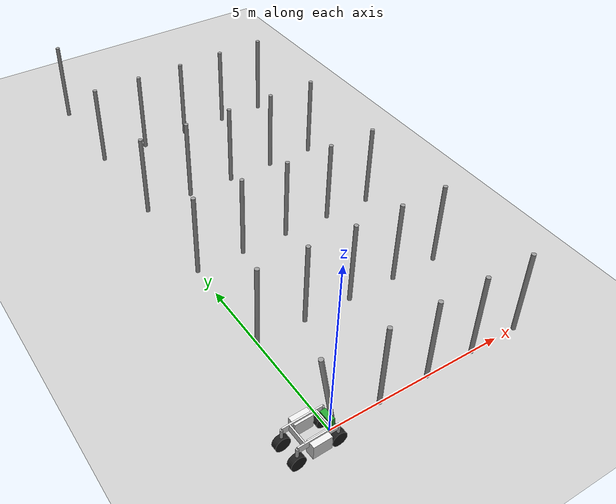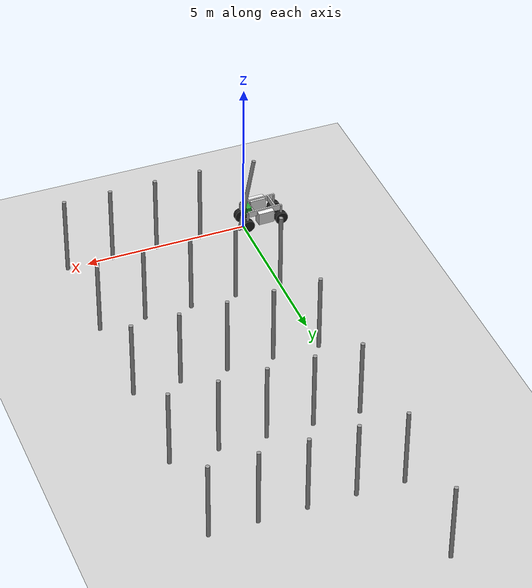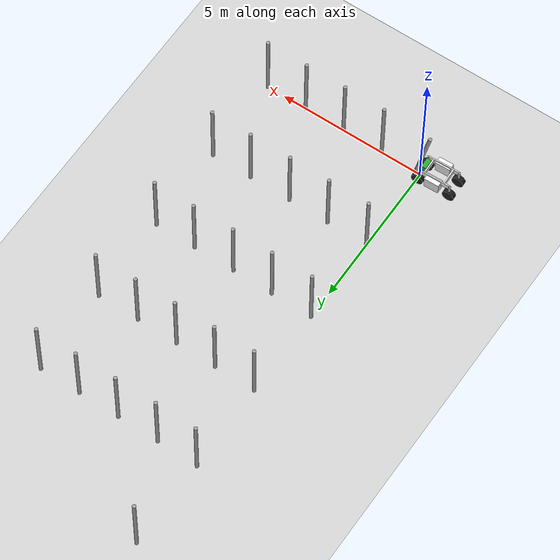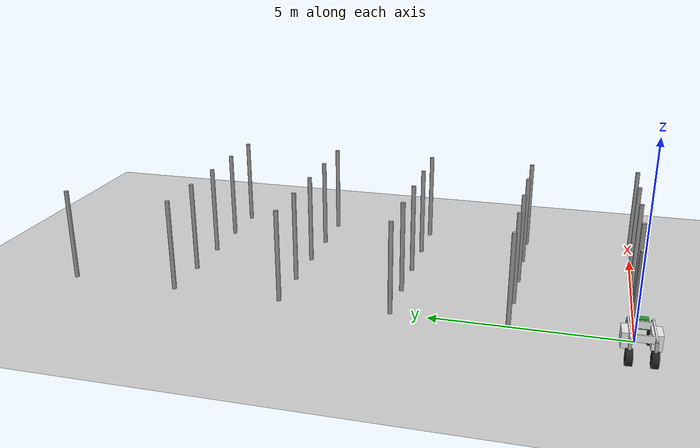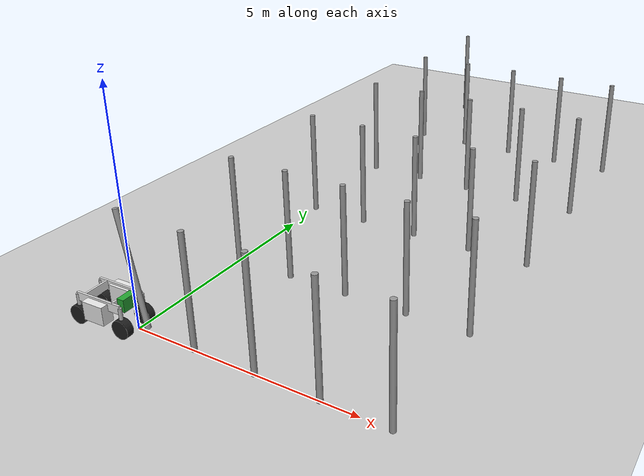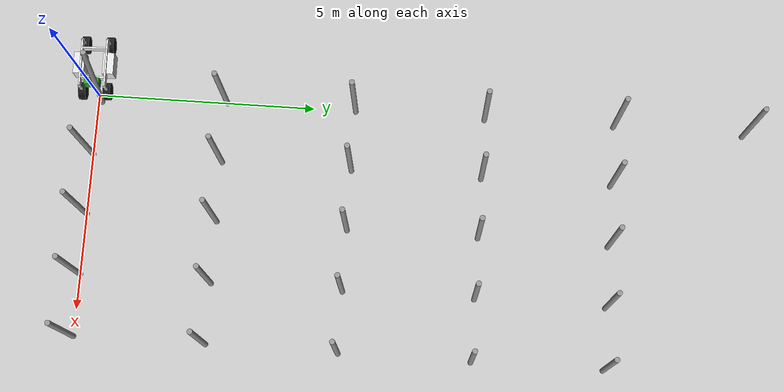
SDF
<sdf version="1.6">
 <world name="default">
  <light name="sun" type="directional">
   <pose>0 0 10 0 -0 0</pose>
   <diffuse>0.8 0.8 0.8 1</diffuse>
   <specular>0.1 0.1 0.1 1</specular>
   <attenuation>
    <range>1000</range>
    <constant>0.9</constant>
    <linear>0.01</linear>
    <quadratic>0.001</quadratic>
   </attenuation>
   <direction>-0.5 0.5 -1</direction>
  </light>
  <model name="ground_plane">
   <static>1</static>
   <link name="link">
    <collision name="collision">
     <geometry><plane><normal>0 0 1</normal><size>100 100</size></plane></geometry>
     <surface><friction><ode><mu>100</mu><mu2>50</mu2></ode></friction></surface>
    </collision>
    <visual name="visual">
     <cast_shadows>0</cast_shadows>
     <geometry><plane><normal>0 0 1</normal><size>100 100</size></plane></geometry>
     <material>
      <script><uri>file://media/materials/scripts/gazebo.material</uri><name>Gazebo/Grey</name></script>
     </material>
    </visual>
   </link>
  </model>
  <gravity>0 0 -9.8</gravity>
  <magnetic_field>6e-06 2.3e-05 -4.2e-05</magnetic_field>
  <atmosphere type="adiabatic"/>
  <physics name="default_physics" default="0" type="ode">
   <max_step_size>0.001</max_step_size>
   <real_time_factor>1</real_time_factor>
   <real_time_update_rate>1000</real_time_update_rate>
  </physics>
  <scene><ambient>0.4 0.4 0.4 1</ambient><background>0.7 0.7 0.7 1</background><shadows>1</shadows></scene>
  <spherical_coordinates>
   <surface_model>EARTH_WGS84</surface_model>
   <latitude_deg>0</latitude_deg>
   <longitude_deg>0</longitude_deg>
   <elevation>0</elevation>
   <heading_deg>0</heading_deg>
  </spherical_coordinates>
  <model name="pole_4">
   <link name="link_0">
    <inertial>
     <mass>0.0364582</mass>
     <inertia>
      <ixx>0.00312124</ixx>
      <ixy>0</ixy>
      <ixz>0</ixz>
      <iyy>0.00312124</iyy>
      <iyz>0</iyz>
      <izz>0.00016615</izz>
     </inertia>
    </inertial>
    <visual name="visual">
     <geometry><cylinder><radius>0.06</radius><length>2.5</length></cylinder></geometry>
     <material>
      <lighting>1</lighting>
      <script><uri>file://media/materials/scripts/gazebo.material</uri><name>Gazebo/Grey</name></script>
      <ambient>0.3 0.3 0.3 1</ambient>
      <diffuse>0.7 0.7 0.7 1</diffuse>
      <specular>0.01 0.01 0.01 1</specular>
      <emissive>0 0 0 1</emissive>
      <shader type="vertex"><normal_map>__default__</normal_map></shader>
     </material>
    </visual>
    <collision name="collision">
     <geometry><cylinder><radius>0.06</radius><length>2.5</length></cylinder></geometry>
     <surface>
      <friction>
       <ode><mu>1</mu><mu2>1</mu2><fdir1>0 0 0</fdir1><slip1>0</slip1><slip2>0</slip2></ode>
       <torsional>
        <coefficient>1</coefficient>
        <patch_radius>0</patch_radius>
        <surface_radius>0</surface_radius>
        <use_patch_radius>1</use_patch_radius>
        <ode><slip>0</slip></ode>
       </torsional>
      </friction>
      <bounce><restitution_coefficient>0</restitution_coefficient><threshold>1e+06</threshold></bounce>
      <contact>
       <collide_without_contact>0</collide_without_contact>
       <collide_without_contact_bitmask>1</collide_without_contact_bitmask>
       <collide_bitmask>1</collide_bitmask>
       <ode>
        <soft_cfm>0</soft_cfm>
        <soft_erp>0.2</soft_erp>
        <kp>1e+13</kp>
        <kd>1</kd>
        <max_vel>0.01</max_vel>
        <min_depth>0</min_depth>
       </ode>
       <bullet>
        <split_impulse>1</split_impulse>
        <split_impulse_penetration_threshold>-0.01</split_impulse_penetration_threshold>
        <soft_cfm>0</soft_cfm>
        <soft_erp>0.2</soft_erp>
        <kp>1e+13</kp>
        <kd>1</kd>
       </bullet>
      </contact>
     </surface>
    </collision>
   </link>
   <static>0</static>
   <pose>-0.066321 0.086478 1.24049 -0.07787 -0.16264 0.41803</pose>
  </model>
  <model name="pole_8">
   <link name="link_0">
    <inertial>
     <mass>0.0364582</mass>
     <inertia>
      <ixx>0.00312124</ixx>
      <ixy>0</ixy>
      <ixz>0</ixz>
      <iyy>0.00312124</iyy>
      <iyz>0</iyz>
      <izz>0.00016615</izz>
     </inertia>
    </inertial>
    <visual name="visual">
     <geometry><cylinder><radius>0.06</radius><length>2.5</length></cylinder></geometry>
     <material>
      <lighting>1</lighting>
      <script><uri>file://media/materials/scripts/gazebo.material</uri><name>Gazebo/Grey</name></script>
      <ambient>0.3 0.3 0.3 1</ambient>
      <diffuse>0.7 0.7 0.7 1</diffuse>
      <specular>0.01 0.01 0.01 1</specular>
      <emissive>0 0 0 1</emissive>
      <shader type="vertex"><normal_map>__default__</normal_map></shader>
     </material>
    </visual>
    <collision name="collision">
     <geometry><cylinder><radius>0.06</radius><length>2.5</length></cylinder></geometry>
     <surface>
      <friction>
       <ode><mu>1</mu><mu2>1</mu2><fdir1>0 0 0</fdir1><slip1>0</slip1><slip2>0</slip2></ode>
       <torsional>
        <coefficient>1</coefficient>
        <patch_radius>0</patch_radius>
        <surface_radius>0</surface_radius>
        <use_patch_radius>1</use_patch_radius>
        <ode><slip>0</slip></ode>
       </torsional>
      </friction>
      <bounce><restitution_coefficient>0</restitution_coefficient><threshold>1e+06</threshold></bounce>
      <contact>
       <collide_without_contact>0</collide_without_contact>
       <collide_without_contact_bitmask>1</collide_without_contact_bitmask>
       <collide_bitmask>1</collide_bitmask>
       <ode>
        <soft_cfm>0</soft_cfm>
        <soft_erp>0.2</soft_erp>
        <kp>1e+13</kp>
        <kd>1</kd>
        <max_vel>0.01</max_vel>
        <min_depth>0</min_depth>
       </ode>
       <bullet>
        <split_impulse>1</split_impulse>
        <split_impulse_penetration_threshold>-0.01</split_impulse_penetration_threshold>
        <soft_cfm>0</soft_cfm>
        <soft_erp>0.2</soft_erp>
        <kp>1e+13</kp>
        <kd>1</kd>
       </bullet>
      </contact>
     </surface>
    </collision>
   </link>
   <static>0</static>
   <pose>1.40414 0.001004 1.24999 -1e-06 1e-06 -0.013206</pose>
  </model>
  <model name="pole_9">
   <link name="link_0">
    <inertial>
     <mass>0.0364582</mass>
     <inertia>
      <ixx>0.00312124</ixx>
      <ixy>0</ixy>
      <ixz>0</ixz>
      <iyy>0.00312124</iyy>
      <iyz>0</iyz>
      <izz>0.00016615</izz>
     </inertia>
    </inertial>
    <visual name="visual">
     <geometry><cylinder><radius>0.06</radius><length>2.5</length></cylinder></geometry>
     <material>
      <lighting>1</lighting>
      <script><uri>file://media/materials/scripts/gazebo.material</uri><name>Gazebo/Grey</name></script>
      <ambient>0.3 0.3 0.3 1</ambient>
      <diffuse>0.7 0.7 0.7 1</diffuse>
      <specular>0.01 0.01 0.01 1</specular>
      <emissive>0 0 0 1</emissive>
      <shader type="vertex"><normal_map>__default__</normal_map></shader>
     </material>
    </visual>
    <collision name="collision">
     <geometry><cylinder><radius>0.06</radius><length>2.5</length></cylinder></geometry>
     <surface>
      <friction>
       <ode><mu>1</mu><mu2>1</mu2><fdir1>0 0 0</fdir1><slip1>0</slip1><slip2>0</slip2></ode>
       <torsional>
        <coefficient>1</coefficient>
        <patch_radius>0</patch_radius>
        <surface_radius>0</surface_radius>
        <use_patch_radius>1</use_patch_radius>
        <ode><slip>0</slip></ode>
       </torsional>
      </friction>
      <bounce><restitution_coefficient>0</restitution_coefficient><threshold>1e+06</threshold></bounce>
      <contact>
       <collide_without_contact>0</collide_without_contact>
       <collide_without_contact_bitmask>1</collide_without_contact_bitmask>
       <collide_bitmask>1</collide_bitmask>
       <ode>
        <soft_cfm>0</soft_cfm>
        <soft_erp>0.2</soft_erp>
        <kp>1e+13</kp>
        <kd>1</kd>
        <max_vel>0.01</max_vel>
        <min_depth>0</min_depth>
       </ode>
       <bullet>
        <split_impulse>1</split_impulse>
        <split_impulse_penetration_threshold>-0.01</split_impulse_penetration_threshold>
        <soft_cfm>0</soft_cfm>
        <soft_erp>0.2</soft_erp>
        <kp>1e+13</kp>
        <kd>1</kd>
       </bullet>
      </contact>
     </surface>
    </collision>
   </link>
   <static>0</static>
   <pose>2.80796 0.001137 1.24999 0 2e-06 -0.031849</pose>
  </model>
  <model name="pole_10">
   <link name="link_0">
    <inertial>
     <mass>0.0364582</mass>
     <inertia>
      <ixx>0.00312124</ixx>
      <ixy>0</ixy>
      <ixz>0</ixz>
      <iyy>0.00312124</iyy>
      <iyz>0</iyz>
      <izz>0.00016615</izz>
     </inertia>
    </inertial>
    <visual name="visual">
     <geometry><cylinder><radius>0.06</radius><length>2.5</length></cylinder></geometry>
     <material>
      <lighting>1</lighting>
      <script><uri>file://media/materials/scripts/gazebo.material</uri><name>Gazebo/Grey</name></script>
      <ambient>0.3 0.3 0.3 1</ambient>
      <diffuse>0.7 0.7 0.7 1</diffuse>
      <specular>0.01 0.01 0.01 1</specular>
      <emissive>0 0 0 1</emissive>
      <shader type="vertex"><normal_map>__default__</normal_map></shader>
     </material>
    </visual>
    <collision name="collision">
     <geometry><cylinder><radius>0.06</radius><length>2.5</length></cylinder></geometry>
     <surface>
      <friction>
       <ode><mu>1</mu><mu2>1</mu2><fdir1>0 0 0</fdir1><slip1>0</slip1><slip2>0</slip2></ode>
       <torsional>
        <coefficient>1</coefficient>
        <patch_radius>0</patch_radius>
        <surface_radius>0</surface_radius>
        <use_patch_radius>1</use_patch_radius>
        <ode><slip>0</slip></ode>
       </torsional>
      </friction>
      <bounce><restitution_coefficient>0</restitution_coefficient><threshold>1e+06</threshold></bounce>
      <contact>
       <collide_without_contact>0</collide_without_contact>
       <collide_without_contact_bitmask>1</collide_without_contact_bitmask>
       <collide_bitmask>1</collide_bitmask>
       <ode>
        <soft_cfm>0</soft_cfm>
        <soft_erp>0.2</soft_erp>
        <kp>1e+13</kp>
        <kd>1</kd>
        <max_vel>0.01</max_vel>
        <min_depth>0</min_depth>
       </ode>
       <bullet>
        <split_impulse>1</split_impulse>
        <split_impulse_penetration_threshold>-0.01</split_impulse_penetration_threshold>
        <soft_cfm>0</soft_cfm>
        <soft_erp>0.2</soft_erp>
        <kp>1e+13</kp>
        <kd>1</kd>
       </bullet>
      </contact>
     </surface>
    </collision>
   </link>
   <static>0</static>
   <pose>4.2039 0.001188 1.25 -1e-06 1e-06 -0.016033</pose>
  </model>
  <model name="pole_11">
   <link name="link_0">
    <inertial>
     <mass>0.0364582</mass>
     <inertia>
      <ixx>0.00312124</ixx>
      <ixy>0</ixy>
      <ixz>0</ixz>
      <iyy>0.00312124</iyy>
      <iyz>0</iyz>
      <izz>0.00016615</izz>
     </inertia>
    </inertial>
    <visual name="visual">
     <geometry><cylinder><radius>0.06</radius><length>2.5</length></cylinder></geometry>
     <material>
      <lighting>1</lighting>
      <script><uri>file://media/materials/scripts/gazebo.material</uri><name>Gazebo/Grey</name></script>
      <ambient>0.3 0.3 0.3 1</ambient>
      <diffuse>0.7 0.7 0.7 1</diffuse>
      <specular>0.01 0.01 0.01 1</specular>
      <emissive>0 0 0 1</emissive>
      <shader type="vertex"><normal_map>__default__</normal_map></shader>
     </material>
    </visual>
    <collision name="collision">
     <geometry><cylinder><radius>0.06</radius><length>2.5</length></cylinder></geometry>
     <surface>
      <friction>
       <ode><mu>1</mu><mu2>1</mu2><fdir1>0 0 0</fdir1><slip1>0</slip1><slip2>0</slip2></ode>
       <torsional>
        <coefficient>1</coefficient>
        <patch_radius>0</patch_radius>
        <surface_radius>0</surface_radius>
        <use_patch_radius>1</use_patch_radius>
        <ode><slip>0</slip></ode>
       </torsional>
      </friction>
      <bounce><restitution_coefficient>0</restitution_coefficient><threshold>1e+06</threshold></bounce>
      <contact>
       <collide_without_contact>0</collide_without_contact>
       <collide_without_contact_bitmask>1</collide_without_contact_bitmask>
       <collide_bitmask>1</collide_bitmask>
       <ode>
        <soft_cfm>0</soft_cfm>
        <soft_erp>0.2</soft_erp>
        <kp>1e+13</kp>
        <kd>1</kd>
        <max_vel>0.01</max_vel>
        <min_depth>0</min_depth>
       </ode>
       <bullet>
        <split_impulse>1</split_impulse>
        <split_impulse_penetration_threshold>-0.01</split_impulse_penetration_threshold>
        <soft_cfm>0</soft_cfm>
        <soft_erp>0.2</soft_erp>
        <kp>1e+13</kp>
        <kd>1</kd>
       </bullet>
      </contact>
     </surface>
    </collision>
   </link>
   <static>0</static>
   <pose>5.61616 0.000904 1.25 -1e-06 1e-06 -0.014818</pose>
  </model>
  <model name="pole_11_clone">
   <link name="link_0">
    <inertial>
     <mass>0.0364582</mass>
     <inertia>
      <ixx>0.00312124</ixx>
      <ixy>0</ixy>
      <ixz>0</ixz>
      <iyy>0.00312124</iyy>
      <iyz>0</iyz>
      <izz>0.00016615</izz>
     </inertia>
    </inertial>
    <visual name="visual">
     <geometry><cylinder><radius>0.06</radius><length>2.5</length></cylinder></geometry>
     <material>
      <lighting>1</lighting>
      <script><uri>file://media/materials/scripts/gazebo.material</uri><name>Gazebo/Grey</name></script>
      <ambient>0.3 0.3 0.3 1</ambient>
      <diffuse>0.7 0.7 0.7 1</diffuse>
      <specular>0.01 0.01 0.01 1</specular>
      <emissive>0 0 0 1</emissive>
      <shader type="vertex"><normal_map>__default__</normal_map></shader>
     </material>
    </visual>
    <collision name="collision">
     <geometry><cylinder><radius>0.06</radius><length>2.5</length></cylinder></geometry>
     <surface>
      <friction>
       <ode><mu>1</mu><mu2>1</mu2><fdir1>0 0 0</fdir1><slip1>0</slip1><slip2>0</slip2></ode>
       <torsional>
        <coefficient>1</coefficient>
        <patch_radius>0</patch_radius>
        <surface_radius>0</surface_radius>
        <use_patch_radius>1</use_patch_radius>
        <ode><slip>0</slip></ode>
       </torsional>
      </friction>
      <bounce><restitution_coefficient>0</restitution_coefficient><threshold>1e+06</threshold></bounce>
      <contact>
       <collide_without_contact>0</collide_without_contact>
       <collide_without_contact_bitmask>1</collide_without_contact_bitmask>
       <collide_bitmask>1</collide_bitmask>
       <ode>
        <soft_cfm>0</soft_cfm>
        <soft_erp>0.2</soft_erp>
        <kp>1e+13</kp>
        <kd>1</kd>
        <max_vel>0.01</max_vel>
        <min_depth>0</min_depth>
       </ode>
       <bullet>
        <split_impulse>1</split_impulse>
        <split_impulse_penetration_threshold>-0.01</split_impulse_penetration_threshold>
        <soft_cfm>0</soft_cfm>
        <soft_erp>0.2</soft_erp>
        <kp>1e+13</kp>
        <kd>1</kd>
       </bullet>
      </contact>
     </surface>
    </collision>
   </link>
   <static>0</static>
   <pose>0.000165 2.98108 1.24999 -1e-06 1e-06 -0.014085</pose>
  </model>
  <model name="pole">
   <link name="link_0">
    <inertial>
     <mass>0.0364582</mass>
     <inertia>
      <ixx>0.00312124</ixx>
      <ixy>0</ixy>
      <ixz>0</ixz>
      <iyy>0.00312124</iyy>
      <iyz>0</iyz>
      <izz>0.00016615</izz>
     </inertia>
    </inertial>
    <visual name="visual">
     <geometry><cylinder><radius>0.06</radius><length>2.5</length></cylinder></geometry>
     <material>
      <lighting>1</lighting>
      <script><uri>file://media/materials/scripts/gazebo.material</uri><name>Gazebo/Grey</name></script>
      <ambient>0.3 0.3 0.3 1</ambient>
      <diffuse>0.7 0.7 0.7 1</diffuse>
      <specular>0.01 0.01 0.01 1</specular>
      <emissive>0 0 0 1</emissive>
      <shader type="vertex"><normal_map>__default__</normal_map></shader>
     </material>
    </visual>
    <collision name="collision">
     <geometry><cylinder><radius>0.06</radius><length>2.5</length></cylinder></geometry>
     <surface>
      <friction>
       <ode><mu>1</mu><mu2>1</mu2><fdir1>0 0 0</fdir1><slip1>0</slip1><slip2>0</slip2></ode>
       <torsional>
        <coefficient>1</coefficient>
        <patch_radius>0</patch_radius>
        <surface_radius>0</surface_radius>
        <use_patch_radius>1</use_patch_radius>
        <ode><slip>0</slip></ode>
       </torsional>
      </friction>
      <bounce><restitution_coefficient>0</restitution_coefficient><threshold>1e+06</threshold></bounce>
      <contact>
       <collide_without_contact>0</collide_without_contact>
       <collide_without_contact_bitmask>1</collide_without_contact_bitmask>
       <collide_bitmask>1</collide_bitmask>
       <ode>
        <soft_cfm>0</soft_cfm>
        <soft_erp>0.2</soft_erp>
        <kp>1e+13</kp>
        <kd>1</kd>
        <max_vel>0.01</max_vel>
        <min_depth>0</min_depth>
       </ode>
       <bullet>
        <split_impulse>1</split_impulse>
        <split_impulse_penetration_threshold>-0.01</split_impulse_penetration_threshold>
        <soft_cfm>0</soft_cfm>
        <soft_erp>0.2</soft_erp>
        <kp>1e+13</kp>
        <kd>1</kd>
       </bullet>
      </contact>
     </surface>
    </collision>
   </link>
   <static>0</static>
   <pose>0.006622 5.96073 1.25 -1e-06 -1e-06 -0.009542</pose>
  </model>
  <model name="pole_0">
   <link name="link_0">
    <inertial>
     <mass>0.0364582</mass>
     <inertia>
      <ixx>0.00312124</ixx>
      <ixy>0</ixy>
      <ixz>0</ixz>
      <iyy>0.00312124</iyy>
      <iyz>0</iyz>
      <izz>0.00016615</izz>
     </inertia>
    </inertial>
    <visual name="visual">
     <geometry><cylinder><radius>0.06</radius><length>2.5</length></cylinder></geometry>
     <material>
      <lighting>1</lighting>
      <script><uri>file://media/materials/scripts/gazebo.material</uri><name>Gazebo/Grey</name></script>
      <ambient>0.3 0.3 0.3 1</ambient>
      <diffuse>0.7 0.7 0.7 1</diffuse>
      <specular>0.01 0.01 0.01 1</specular>
      <emissive>0 0 0 1</emissive>
      <shader type="vertex"><normal_map>__default__</normal_map></shader>
     </material>
    </visual>
    <collision name="collision">
     <geometry><cylinder><radius>0.06</radius><length>2.5</length></cylinder></geometry>
     <surface>
      <friction>
       <ode><mu>1</mu><mu2>1</mu2><fdir1>0 0 0</fdir1><slip1>0</slip1><slip2>0</slip2></ode>
       <torsional>
        <coefficient>1</coefficient>
        <patch_radius>0</patch_radius>
        <surface_radius>0</surface_radius>
        <use_patch_radius>1</use_patch_radius>
        <ode><slip>0</slip></ode>
       </torsional>
      </friction>
      <bounce><restitution_coefficient>0</restitution_coefficient><threshold>1e+06</threshold></bounce>
      <contact>
       <collide_without_contact>0</collide_without_contact>
       <collide_without_contact_bitmask>1</collide_without_contact_bitmask>
       <collide_bitmask>1</collide_bitmask>
       <ode>
        <soft_cfm>0</soft_cfm>
        <soft_erp>0.2</soft_erp>
        <kp>1e+13</kp>
        <kd>1</kd>
        <max_vel>0.01</max_vel>
        <min_depth>0</min_depth>
       </ode>
       <bullet>
        <split_impulse>1</split_impulse>
        <split_impulse_penetration_threshold>-0.01</split_impulse_penetration_threshold>
        <soft_cfm>0</soft_cfm>
        <soft_erp>0.2</soft_erp>
        <kp>1e+13</kp>
        <kd>1</kd>
       </bullet>
      </contact>
     </surface>
    </collision>
   </link>
   <static>0</static>
   <pose>0.013431 8.94089 1.25 1e-06 3e-06 -0.011813</pose>
  </model>
  <model name="pole_1">
   <link name="link_0">
    <inertial>
     <mass>0.0364582</mass>
     <inertia>
      <ixx>0.00312124</ixx>
      <ixy>0</ixy>
      <ixz>0</ixz>
      <iyy>0.00312124</iyy>
      <iyz>0</iyz>
      <izz>0.00016615</izz>
     </inertia>
    </inertial>
    <visual name="visual">
     <geometry><cylinder><radius>0.06</radius><length>2.5</length></cylinder></geometry>
     <material>
      <lighting>1</lighting>
      <script><uri>file://media/materials/scripts/gazebo.material</uri><name>Gazebo/Grey</name></script>
      <ambient>0.3 0.3 0.3 1</ambient>
      <diffuse>0.7 0.7 0.7 1</diffuse>
      <specular>0.01 0.01 0.01 1</specular>
      <emissive>0 0 0 1</emissive>
      <shader type="vertex"><normal_map>__default__</normal_map></shader>
     </material>
    </visual>
    <collision name="collision">
     <geometry><cylinder><radius>0.06</radius><length>2.5</length></cylinder></geometry>
     <surface>
      <friction>
       <ode><mu>1</mu><mu2>1</mu2><fdir1>0 0 0</fdir1><slip1>0</slip1><slip2>0</slip2></ode>
       <torsional>
        <coefficient>1</coefficient>
        <patch_radius>0</patch_radius>
        <surface_radius>0</surface_radius>
        <use_patch_radius>1</use_patch_radius>
        <ode><slip>0</slip></ode>
       </torsional>
      </friction>
      <bounce><restitution_coefficient>0</restitution_coefficient><threshold>1e+06</threshold></bounce>
      <contact>
       <collide_without_contact>0</collide_without_contact>
       <collide_without_contact_bitmask>1</collide_without_contact_bitmask>
       <collide_bitmask>1</collide_bitmask>
       <ode>
        <soft_cfm>0</soft_cfm>
        <soft_erp>0.2</soft_erp>
        <kp>1e+13</kp>
        <kd>1</kd>
        <max_vel>0.01</max_vel>
        <min_depth>0</min_depth>
       </ode>
       <bullet>
        <split_impulse>1</split_impulse>
        <split_impulse_penetration_threshold>-0.01</split_impulse_penetration_threshold>
        <soft_cfm>0</soft_cfm>
        <soft_erp>0.2</soft_erp>
        <kp>1e+13</kp>
        <kd>1</kd>
       </bullet>
      </contact>
     </surface>
    </collision>
   </link>
   <static>0</static>
   <pose>-0.008182 11.9208 1.24999 0 -2e-06 -0.013332</pose>
  </model>
  <model name="pole_2">
   <link name="link_0">
    <inertial>
     <mass>0.0364582</mass>
     <inertia>
      <ixx>0.00312124</ixx>
      <ixy>0</ixy>
      <ixz>0</ixz>
      <iyy>0.00312124</iyy>
      <iyz>0</iyz>
      <izz>0.00016615</izz>
     </inertia>
    </inertial>
    <visual name="visual">
     <geometry><cylinder><radius>0.06</radius><length>2.5</length></cylinder></geometry>
     <material>
      <lighting>1</lighting>
      <script><uri>file://media/materials/scripts/gazebo.material</uri><name>Gazebo/Grey</name></script>
      <ambient>0.3 0.3 0.3 1</ambient>
      <diffuse>0.7 0.7 0.7 1</diffuse>
      <specular>0.01 0.01 0.01 1</specular>
      <emissive>0 0 0 1</emissive>
      <shader type="vertex"><normal_map>__default__</normal_map></shader>
     </material>
    </visual>
    <collision name="collision">
     <geometry><cylinder><radius>0.06</radius><length>2.5</length></cylinder></geometry>
     <surface>
      <friction>
       <ode><mu>1</mu><mu2>1</mu2><fdir1>0 0 0</fdir1><slip1>0</slip1><slip2>0</slip2></ode>
       <torsional>
        <coefficient>1</coefficient>
        <patch_radius>0</patch_radius>
        <surface_radius>0</surface_radius>
        <use_patch_radius>1</use_patch_radius>
        <ode><slip>0</slip></ode>
       </torsional>
      </friction>
      <bounce><restitution_coefficient>0</restitution_coefficient><threshold>1e+06</threshold></bounce>
      <contact>
       <collide_without_contact>0</collide_without_contact>
       <collide_without_contact_bitmask>1</collide_without_contact_bitmask>
       <collide_bitmask>1</collide_bitmask>
       <ode>
        <soft_cfm>0</soft_cfm>
        <soft_erp>0.2</soft_erp>
        <kp>1e+13</kp>
        <kd>1</kd>
        <max_vel>0.01</max_vel>
        <min_depth>0</min_depth>
       </ode>
       <bullet>
        <split_impulse>1</split_impulse>
        <split_impulse_penetration_threshold>-0.01</split_impulse_penetration_threshold>
        <soft_cfm>0</soft_cfm>
        <soft_erp>0.2</soft_erp>
        <kp>1e+13</kp>
        <kd>1</kd>
       </bullet>
      </contact>
     </surface>
    </collision>
   </link>
   <static>0</static>
   <pose>0.027485 14.8937 1.25 0 2e-06 0.22432</pose>
  </model>
  <model name="pole_3">
   <link name="link_0">
    <inertial>
     <mass>0.0364582</mass>
     <inertia>
      <ixx>0.00312124</ixx>
      <ixy>0</ixy>
      <ixz>0</ixz>
      <iyy>0.00312124</iyy>
      <iyz>0</iyz>
      <izz>0.00016615</izz>
     </inertia>
    </inertial>
    <visual name="visual">
     <geometry><cylinder><radius>0.06</radius><length>2.5</length></cylinder></geometry>
     <material>
      <lighting>1</lighting>
      <script><uri>file://media/materials/scripts/gazebo.material</uri><name>Gazebo/Grey</name></script>
      <ambient>0.3 0.3 0.3 1</ambient>
      <diffuse>0.7 0.7 0.7 1</diffuse>
      <specular>0.01 0.01 0.01 1</specular>
      <emissive>0 0 0 1</emissive>
      <shader type="vertex"><normal_map>__default__</normal_map></shader>
     </material>
    </visual>
    <collision name="collision">
     <geometry><cylinder><radius>0.06</radius><length>2.5</length></cylinder></geometry>
     <surface>
      <friction>
       <ode><mu>1</mu><mu2>1</mu2><fdir1>0 0 0</fdir1><slip1>0</slip1><slip2>0</slip2></ode>
       <torsional>
        <coefficient>1</coefficient>
        <patch_radius>0</patch_radius>
        <surface_radius>0</surface_radius>
        <use_patch_radius>1</use_patch_radius>
        <ode><slip>0</slip></ode>
       </torsional>
      </friction>
      <bounce><restitution_coefficient>0</restitution_coefficient><threshold>1e+06</threshold></bounce>
      <contact>
       <collide_without_contact>0</collide_without_contact>
       <collide_without_contact_bitmask>1</collide_without_contact_bitmask>
       <collide_bitmask>1</collide_bitmask>
       <ode>
        <soft_cfm>0</soft_cfm>
        <soft_erp>0.2</soft_erp>
        <kp>1e+13</kp>
        <kd>1</kd>
        <max_vel>0.01</max_vel>
        <min_depth>0</min_depth>
       </ode>
       <bullet>
        <split_impulse>1</split_impulse>
        <split_impulse_penetration_threshold>-0.01</split_impulse_penetration_threshold>
        <soft_cfm>0</soft_cfm>
        <soft_erp>0.2</soft_erp>
        <kp>1e+13</kp>
        <kd>1</kd>
       </bullet>
      </contact>
     </surface>
    </collision>
   </link>
   <static>0</static>
   <pose>1.40465 2.98071 1.25 -1e-06 -1e-06 -0.008966</pose>
  </model>
  <model name="pole_5">
   <link name="link_0">
    <inertial>
     <mass>0.0364582</mass>
     <inertia>
      <ixx>0.00312124</ixx>
      <ixy>0</ixy>
      <ixz>0</ixz>
      <iyy>0.00312124</iyy>
      <iyz>0</iyz>
      <izz>0.00016615</izz>
     </inertia>
    </inertial>
    <visual name="visual">
     <geometry><cylinder><radius>0.06</radius><length>2.5</length></cylinder></geometry>
     <material>
      <lighting>1</lighting>
      <script><uri>file://media/materials/scripts/gazebo.material</uri><name>Gazebo/Grey</name></script>
      <ambient>0.3 0.3 0.3 1</ambient>
      <diffuse>0.7 0.7 0.7 1</diffuse>
      <specular>0.01 0.01 0.01 1</specular>
      <emissive>0 0 0 1</emissive>
      <shader type="vertex"><normal_map>__default__</normal_map></shader>
     </material>
    </visual>
    <collision name="collision">
     <geometry><cylinder><radius>0.06</radius><length>2.5</length></cylinder></geometry>
     <surface>
      <friction>
       <ode><mu>1</mu><mu2>1</mu2><fdir1>0 0 0</fdir1><slip1>0</slip1><slip2>0</slip2></ode>
       <torsional>
        <coefficient>1</coefficient>
        <patch_radius>0</patch_radius>
        <surface_radius>0</surface_radius>
        <use_patch_radius>1</use_patch_radius>
        <ode><slip>0</slip></ode>
       </torsional>
      </friction>
      <bounce><restitution_coefficient>0</restitution_coefficient><threshold>1e+06</threshold></bounce>
      <contact>
       <collide_without_contact>0</collide_without_contact>
       <collide_without_contact_bitmask>1</collide_without_contact_bitmask>
       <collide_bitmask>1</collide_bitmask>
       <ode>
        <soft_cfm>0</soft_cfm>
        <soft_erp>0.2</soft_erp>
        <kp>1e+13</kp>
        <kd>1</kd>
        <max_vel>0.01</max_vel>
        <min_depth>0</min_depth>
       </ode>
       <bullet>
        <split_impulse>1</split_impulse>
        <split_impulse_penetration_threshold>-0.01</split_impulse_penetration_threshold>
        <soft_cfm>0</soft_cfm>
        <soft_erp>0.2</soft_erp>
        <kp>1e+13</kp>
        <kd>1</kd>
       </bullet>
      </contact>
     </surface>
    </collision>
   </link>
   <static>0</static>
   <pose>2.79575 2.98061 1.24999 -0 1e-06 -0.008356</pose>
  </model>
  <model name="pole_6">
   <link name="link_0">
    <inertial>
     <mass>0.0364582</mass>
     <inertia>
      <ixx>0.00312124</ixx>
      <ixy>0</ixy>
      <ixz>0</ixz>
      <iyy>0.00312124</iyy>
      <iyz>0</iyz>
      <izz>0.00016615</izz>
     </inertia>
    </inertial>
    <visual name="visual">
     <geometry><cylinder><radius>0.06</radius><length>2.5</length></cylinder></geometry>
     <material>
      <lighting>1</lighting>
      <script><uri>file://media/materials/scripts/gazebo.material</uri><name>Gazebo/Grey</name></script>
      <ambient>0.3 0.3 0.3 1</ambient>
      <diffuse>0.7 0.7 0.7 1</diffuse>
      <specular>0.01 0.01 0.01 1</specular>
      <emissive>0 0 0 1</emissive>
      <shader type="vertex"><normal_map>__default__</normal_map></shader>
     </material>
    </visual>
    <collision name="collision">
     <geometry><cylinder><radius>0.06</radius><length>2.5</length></cylinder></geometry>
     <surface>
      <friction>
       <ode><mu>1</mu><mu2>1</mu2><fdir1>0 0 0</fdir1><slip1>0</slip1><slip2>0</slip2></ode>
       <torsional>
        <coefficient>1</coefficient>
        <patch_radius>0</patch_radius>
        <surface_radius>0</surface_radius>
        <use_patch_radius>1</use_patch_radius>
        <ode><slip>0</slip></ode>
       </torsional>
      </friction>
      <bounce><restitution_coefficient>0</restitution_coefficient><threshold>1e+06</threshold></bounce>
      <contact>
       <collide_without_contact>0</collide_without_contact>
       <collide_without_contact_bitmask>1</collide_without_contact_bitmask>
       <collide_bitmask>1</collide_bitmask>
       <ode>
        <soft_cfm>0</soft_cfm>
        <soft_erp>0.2</soft_erp>
        <kp>1e+13</kp>
        <kd>1</kd>
        <max_vel>0.01</max_vel>
        <min_depth>0</min_depth>
       </ode>
       <bullet>
        <split_impulse>1</split_impulse>
        <split_impulse_penetration_threshold>-0.01</split_impulse_penetration_threshold>
        <soft_cfm>0</soft_cfm>
        <soft_erp>0.2</soft_erp>
        <kp>1e+13</kp>
        <kd>1</kd>
       </bullet>
      </contact>
     </surface>
    </collision>
   </link>
   <static>0</static>
   <pose>4.22233 2.98063 1.24999 0 2e-06 -0.007874</pose>
  </model>
  <model name="pole_7">
   <link name="link_0">
    <inertial>
     <mass>0.0364582</mass>
     <inertia>
      <ixx>0.00312124</ixx>
      <ixy>0</ixy>
      <ixz>0</ixz>
      <iyy>0.00312124</iyy>
      <iyz>0</iyz>
      <izz>0.00016615</izz>
     </inertia>
    </inertial>
    <visual name="visual">
     <geometry><cylinder><radius>0.06</radius><length>2.5</length></cylinder></geometry>
     <material>
      <lighting>1</lighting>
      <script><uri>file://media/materials/scripts/gazebo.material</uri><name>Gazebo/Grey</name></script>
      <ambient>0.3 0.3 0.3 1</ambient>
      <diffuse>0.7 0.7 0.7 1</diffuse>
      <specular>0.01 0.01 0.01 1</specular>
      <emissive>0 0 0 1</emissive>
      <shader type="vertex"><normal_map>__default__</normal_map></shader>
     </material>
    </visual>
    <collision name="collision">
     <geometry><cylinder><radius>0.06</radius><length>2.5</length></cylinder></geometry>
     <surface>
      <friction>
       <ode><mu>1</mu><mu2>1</mu2><fdir1>0 0 0</fdir1><slip1>0</slip1><slip2>0</slip2></ode>
       <torsional>
        <coefficient>1</coefficient>
        <patch_radius>0</patch_radius>
        <surface_radius>0</surface_radius>
        <use_patch_radius>1</use_patch_radius>
        <ode><slip>0</slip></ode>
       </torsional>
      </friction>
      <bounce><restitution_coefficient>0</restitution_coefficient><threshold>1e+06</threshold></bounce>
      <contact>
       <collide_without_contact>0</collide_without_contact>
       <collide_without_contact_bitmask>1</collide_without_contact_bitmask>
       <collide_bitmask>1</collide_bitmask>
       <ode>
        <soft_cfm>0</soft_cfm>
        <soft_erp>0.2</soft_erp>
        <kp>1e+13</kp>
        <kd>1</kd>
        <max_vel>0.01</max_vel>
        <min_depth>0</min_depth>
       </ode>
       <bullet>
        <split_impulse>1</split_impulse>
        <split_impulse_penetration_threshold>-0.01</split_impulse_penetration_threshold>
        <soft_cfm>0</soft_cfm>
        <soft_erp>0.2</soft_erp>
        <kp>1e+13</kp>
        <kd>1</kd>
       </bullet>
      </contact>
     </surface>
    </collision>
   </link>
   <static>0</static>
   <pose>5.60726 2.98066 1.25 0 1e-06 -0.007781</pose>
  </model>
  <model name="pole_12">
   <link name="link_0">
    <inertial>
     <mass>0.0364582</mass>
     <inertia>
      <ixx>0.00312124</ixx>
      <ixy>0</ixy>
      <ixz>0</ixz>
      <iyy>0.00312124</iyy>
      <iyz>0</iyz>
      <izz>0.00016615</izz>
     </inertia>
    </inertial>
    <visual name="visual">
     <geometry><cylinder><radius>0.06</radius><length>2.5</length></cylinder></geometry>
     <material>
      <lighting>1</lighting>
      <script><uri>file://media/materials/scripts/gazebo.material</uri><name>Gazebo/Grey</name></script>
      <ambient>0.3 0.3 0.3 1</ambient>
      <diffuse>0.7 0.7 0.7 1</diffuse>
      <specular>0.01 0.01 0.01 1</specular>
      <emissive>0 0 0 1</emissive>
      <shader type="vertex"><normal_map>__default__</normal_map></shader>
     </material>
    </visual>
    <collision name="collision">
     <geometry><cylinder><radius>0.06</radius><length>2.5</length></cylinder></geometry>
     <surface>
      <friction>
       <ode><mu>1</mu><mu2>1</mu2><fdir1>0 0 0</fdir1><slip1>0</slip1><slip2>0</slip2></ode>
       <torsional>
        <coefficient>1</coefficient>
        <patch_radius>0</patch_radius>
        <surface_radius>0</surface_radius>
        <use_patch_radius>1</use_patch_radius>
        <ode><slip>0</slip></ode>
       </torsional>
      </friction>
      <bounce><restitution_coefficient>0</restitution_coefficient><threshold>1e+06</threshold></bounce>
      <contact>
       <collide_without_contact>0</collide_without_contact>
       <collide_without_contact_bitmask>1</collide_without_contact_bitmask>
       <collide_bitmask>1</collide_bitmask>
       <ode>
        <soft_cfm>0</soft_cfm>
        <soft_erp>0.2</soft_erp>
        <kp>1e+13</kp>
        <kd>1</kd>
        <max_vel>0.01</max_vel>
        <min_depth>0</min_depth>
       </ode>
       <bullet>
        <split_impulse>1</split_impulse>
        <split_impulse_penetration_threshold>-0.01</split_impulse_penetration_threshold>
        <soft_cfm>0</soft_cfm>
        <soft_erp>0.2</soft_erp>
        <kp>1e+13</kp>
        <kd>1</kd>
       </bullet>
      </contact>
     </surface>
    </collision>
   </link>
   <static>0</static>
   <pose>1.41354 5.96063 1.25 -1e-06 3e-06 -0.005674</pose>
  </model>
  <model name="pole_13">
   <link name="link_0">
    <inertial>
     <mass>0.0364582</mass>
     <inertia>
      <ixx>0.00312124</ixx>
      <ixy>0</ixy>
      <ixz>0</ixz>
      <iyy>0.00312124</iyy>
      <iyz>0</iyz>
      <izz>0.00016615</izz>
     </inertia>
    </inertial>
    <visual name="visual">
     <geometry><cylinder><radius>0.06</radius><length>2.5</length></cylinder></geometry>
     <material>
      <lighting>1</lighting>
      <script><uri>file://media/materials/scripts/gazebo.material</uri><name>Gazebo/Grey</name></script>
      <ambient>0.3 0.3 0.3 1</ambient>
      <diffuse>0.7 0.7 0.7 1</diffuse>
      <specular>0.01 0.01 0.01 1</specular>
      <emissive>0 0 0 1</emissive>
      <shader type="vertex"><normal_map>__default__</normal_map></shader>
     </material>
    </visual>
    <collision name="collision">
     <geometry><cylinder><radius>0.06</radius><length>2.5</length></cylinder></geometry>
     <surface>
      <friction>
       <ode><mu>1</mu><mu2>1</mu2><fdir1>0 0 0</fdir1><slip1>0</slip1><slip2>0</slip2></ode>
       <torsional>
        <coefficient>1</coefficient>
        <patch_radius>0</patch_radius>
        <surface_radius>0</surface_radius>
        <use_patch_radius>1</use_patch_radius>
        <ode><slip>0</slip></ode>
       </torsional>
      </friction>
      <bounce><restitution_coefficient>0</restitution_coefficient><threshold>1e+06</threshold></bounce>
      <contact>
       <collide_without_contact>0</collide_without_contact>
       <collide_without_contact_bitmask>1</collide_without_contact_bitmask>
       <collide_bitmask>1</collide_bitmask>
       <ode>
        <soft_cfm>0</soft_cfm>
        <soft_erp>0.2</soft_erp>
        <kp>1e+13</kp>
        <kd>1</kd>
        <max_vel>0.01</max_vel>
        <min_depth>0</min_depth>
       </ode>
       <bullet>
        <split_impulse>1</split_impulse>
        <split_impulse_penetration_threshold>-0.01</split_impulse_penetration_threshold>
        <soft_cfm>0</soft_cfm>
        <soft_erp>0.2</soft_erp>
        <kp>1e+13</kp>
        <kd>1</kd>
       </bullet>
      </contact>
     </surface>
    </collision>
   </link>
   <static>0</static>
   <pose>2.80794 5.96064 1.24999 0 0 -0.005336</pose>
  </model>
  <model name="pole_14">
   <link name="link_0">
    <inertial>
     <mass>0.0364582</mass>
     <inertia>
      <ixx>0.00312124</ixx>
      <ixy>0</ixy>
      <ixz>0</ixz>
      <iyy>0.00312124</iyy>
      <iyz>0</iyz>
      <izz>0.00016615</izz>
     </inertia>
    </inertial>
    <visual name="visual">
     <geometry><cylinder><radius>0.06</radius><length>2.5</length></cylinder></geometry>
     <material>
      <lighting>1</lighting>
      <script><uri>file://media/materials/scripts/gazebo.material</uri><name>Gazebo/Grey</name></script>
      <ambient>0.3 0.3 0.3 1</ambient>
      <diffuse>0.7 0.7 0.7 1</diffuse>
      <specular>0.01 0.01 0.01 1</specular>
      <emissive>0 0 0 1</emissive>
      <shader type="vertex"><normal_map>__default__</normal_map></shader>
     </material>
    </visual>
    <collision name="collision">
     <geometry><cylinder><radius>0.06</radius><length>2.5</length></cylinder></geometry>
     <surface>
      <friction>
       <ode><mu>1</mu><mu2>1</mu2><fdir1>0 0 0</fdir1><slip1>0</slip1><slip2>0</slip2></ode>
       <torsional>
        <coefficient>1</coefficient>
        <patch_radius>0</patch_radius>
        <surface_radius>0</surface_radius>
        <use_patch_radius>1</use_patch_radius>
        <ode><slip>0</slip></ode>
       </torsional>
      </friction>
      <bounce><restitution_coefficient>0</restitution_coefficient><threshold>1e+06</threshold></bounce>
      <contact>
       <collide_without_contact>0</collide_without_contact>
       <collide_without_contact_bitmask>1</collide_without_contact_bitmask>
       <collide_bitmask>1</collide_bitmask>
       <ode>
        <soft_cfm>0</soft_cfm>
        <soft_erp>0.2</soft_erp>
        <kp>1e+13</kp>
        <kd>1</kd>
        <max_vel>0.01</max_vel>
        <min_depth>0</min_depth>
       </ode>
       <bullet>
        <split_impulse>1</split_impulse>
        <split_impulse_penetration_threshold>-0.01</split_impulse_penetration_threshold>
        <soft_cfm>0</soft_cfm>
        <soft_erp>0.2</soft_erp>
        <kp>1e+13</kp>
        <kd>1</kd>
       </bullet>
      </contact>
     </surface>
    </collision>
   </link>
   <static>0</static>
   <pose>4.21944 5.96058 1.25 0 1e-06 -0.005596</pose>
  </model>
  <model name="pole_15">
   <link name="link_0">
    <inertial>
     <mass>0.0364582</mass>
     <inertia>
      <ixx>0.00312124</ixx>
      <ixy>0</ixy>
      <ixz>0</ixz>
      <iyy>0.00312124</iyy>
      <iyz>0</iyz>
      <izz>0.00016615</izz>
     </inertia>
    </inertial>
    <visual name="visual">
     <geometry><cylinder><radius>0.06</radius><length>2.5</length></cylinder></geometry>
     <material>
      <lighting>1</lighting>
      <script><uri>file://media/materials/scripts/gazebo.material</uri><name>Gazebo/Grey</name></script>
      <ambient>0.3 0.3 0.3 1</ambient>
      <diffuse>0.7 0.7 0.7 1</diffuse>
      <specular>0.01 0.01 0.01 1</specular>
      <emissive>0 0 0 1</emissive>
      <shader type="vertex"><normal_map>__default__</normal_map></shader>
     </material>
    </visual>
    <collision name="collision">
     <geometry><cylinder><radius>0.06</radius><length>2.5</length></cylinder></geometry>
     <surface>
      <friction>
       <ode><mu>1</mu><mu2>1</mu2><fdir1>0 0 0</fdir1><slip1>0</slip1><slip2>0</slip2></ode>
       <torsional>
        <coefficient>1</coefficient>
        <patch_radius>0</patch_radius>
        <surface_radius>0</surface_radius>
        <use_patch_radius>1</use_patch_radius>
        <ode><slip>0</slip></ode>
       </torsional>
      </friction>
      <bounce><restitution_coefficient>0</restitution_coefficient><threshold>1e+06</threshold></bounce>
      <contact>
       <collide_without_contact>0</collide_without_contact>
       <collide_without_contact_bitmask>1</collide_without_contact_bitmask>
       <collide_bitmask>1</collide_bitmask>
       <ode>
        <soft_cfm>0</soft_cfm>
        <soft_erp>0.2</soft_erp>
        <kp>1e+13</kp>
        <kd>1</kd>
        <max_vel>0.01</max_vel>
        <min_depth>0</min_depth>
       </ode>
       <bullet>
        <split_impulse>1</split_impulse>
        <split_impulse_penetration_threshold>-0.01</split_impulse_penetration_threshold>
        <soft_cfm>0</soft_cfm>
        <soft_erp>0.2</soft_erp>
        <kp>1e+13</kp>
        <kd>1</kd>
       </bullet>
      </contact>
     </surface>
    </collision>
   </link>
   <static>0</static>
   <pose>5.62343 5.96052 1.25 0 1e-06 -0.005556</pose>
  </model>
  <model name="pole_16">
   <link name="link_0">
    <inertial>
     <mass>0.0364582</mass>
     <inertia>
      <ixx>0.00312124</ixx>
      <ixy>0</ixy>
      <ixz>0</ixz>
      <iyy>0.00312124</iyy>
      <iyz>0</iyz>
      <izz>0.00016615</izz>
     </inertia>
    </inertial>
    <visual name="visual">
     <geometry><cylinder><radius>0.06</radius><length>2.5</length></cylinder></geometry>
     <material>
      <lighting>1</lighting>
      <script><uri>file://media/materials/scripts/gazebo.material</uri><name>Gazebo/Grey</name></script>
      <ambient>0.3 0.3 0.3 1</ambient>
      <diffuse>0.7 0.7 0.7 1</diffuse>
      <specular>0.01 0.01 0.01 1</specular>
      <emissive>0 0 0 1</emissive>
      <shader type="vertex"><normal_map>__default__</normal_map></shader>
     </material>
    </visual>
    <collision name="collision">
     <geometry><cylinder><radius>0.06</radius><length>2.5</length></cylinder></geometry>
     <surface>
      <friction>
       <ode><mu>1</mu><mu2>1</mu2><fdir1>0 0 0</fdir1><slip1>0</slip1><slip2>0</slip2></ode>
       <torsional>
        <coefficient>1</coefficient>
        <patch_radius>0</patch_radius>
        <surface_radius>0</surface_radius>
        <use_patch_radius>1</use_patch_radius>
        <ode><slip>0</slip></ode>
       </torsional>
      </friction>
      <bounce><restitution_coefficient>0</restitution_coefficient><threshold>1e+06</threshold></bounce>
      <contact>
       <collide_without_contact>0</collide_without_contact>
       <collide_without_contact_bitmask>1</collide_without_contact_bitmask>
       <collide_bitmask>1</collide_bitmask>
       <ode>
        <soft_cfm>0</soft_cfm>
        <soft_erp>0.2</soft_erp>
        <kp>1e+13</kp>
        <kd>1</kd>
        <max_vel>0.01</max_vel>
        <min_depth>0</min_depth>
       </ode>
       <bullet>
        <split_impulse>1</split_impulse>
        <split_impulse_penetration_threshold>-0.01</split_impulse_penetration_threshold>
        <soft_cfm>0</soft_cfm>
        <soft_erp>0.2</soft_erp>
        <kp>1e+13</kp>
        <kd>1</kd>
       </bullet>
      </contact>
     </surface>
    </collision>
   </link>
   <static>0</static>
   <pose>1.41304 8.9402 1.25 -0 1e-06 -0.006676</pose>
  </model>
  <model name="pole_17">
   <link name="link_0">
    <inertial>
     <mass>0.0364582</mass>
     <inertia>
      <ixx>0.00312124</ixx>
      <ixy>0</ixy>
      <ixz>0</ixz>
      <iyy>0.00312124</iyy>
      <iyz>0</iyz>
      <izz>0.00016615</izz>
     </inertia>
    </inertial>
    <visual name="visual">
     <geometry><cylinder><radius>0.06</radius><length>2.5</length></cylinder></geometry>
     <material>
      <lighting>1</lighting>
      <script><uri>file://media/materials/scripts/gazebo.material</uri><name>Gazebo/Grey</name></script>
      <ambient>0.3 0.3 0.3 1</ambient>
      <diffuse>0.7 0.7 0.7 1</diffuse>
      <specular>0.01 0.01 0.01 1</specular>
      <emissive>0 0 0 1</emissive>
      <shader type="vertex"><normal_map>__default__</normal_map></shader>
     </material>
    </visual>
    <collision name="collision">
     <geometry><cylinder><radius>0.06</radius><length>2.5</length></cylinder></geometry>
     <surface>
      <friction>
       <ode><mu>1</mu><mu2>1</mu2><fdir1>0 0 0</fdir1><slip1>0</slip1><slip2>0</slip2></ode>
       <torsional>
        <coefficient>1</coefficient>
        <patch_radius>0</patch_radius>
        <surface_radius>0</surface_radius>
        <use_patch_radius>1</use_patch_radius>
        <ode><slip>0</slip></ode>
       </torsional>
      </friction>
      <bounce><restitution_coefficient>0</restitution_coefficient><threshold>1e+06</threshold></bounce>
      <contact>
       <collide_without_contact>0</collide_without_contact>
       <collide_without_contact_bitmask>1</collide_without_contact_bitmask>
       <collide_bitmask>1</collide_bitmask>
       <ode>
        <soft_cfm>0</soft_cfm>
        <soft_erp>0.2</soft_erp>
        <kp>1e+13</kp>
        <kd>1</kd>
        <max_vel>0.01</max_vel>
        <min_depth>0</min_depth>
       </ode>
       <bullet>
        <split_impulse>1</split_impulse>
        <split_impulse_penetration_threshold>-0.01</split_impulse_penetration_threshold>
        <soft_cfm>0</soft_cfm>
        <soft_erp>0.2</soft_erp>
        <kp>1e+13</kp>
        <kd>1</kd>
       </bullet>
      </contact>
     </surface>
    </collision>
   </link>
   <static>0</static>
   <pose>2.79979 8.94027 1.25 -1e-06 0 -0.004268</pose>
  </model>
  <model name="pole_18">
   <link name="link_0">
    <inertial>
     <mass>0.0364582</mass>
     <inertia>
      <ixx>0.00312124</ixx>
      <ixy>0</ixy>
      <ixz>0</ixz>
      <iyy>0.00312124</iyy>
      <iyz>0</iyz>
      <izz>0.00016615</izz>
     </inertia>
    </inertial>
    <visual name="visual">
     <geometry><cylinder><radius>0.06</radius><length>2.5</length></cylinder></geometry>
     <material>
      <lighting>1</lighting>
      <script><uri>file://media/materials/scripts/gazebo.material</uri><name>Gazebo/Grey</name></script>
      <ambient>0.3 0.3 0.3 1</ambient>
      <diffuse>0.7 0.7 0.7 1</diffuse>
      <specular>0.01 0.01 0.01 1</specular>
      <emissive>0 0 0 1</emissive>
      <shader type="vertex"><normal_map>__default__</normal_map></shader>
     </material>
    </visual>
    <collision name="collision">
     <geometry><cylinder><radius>0.06</radius><length>2.5</length></cylinder></geometry>
     <surface>
      <friction>
       <ode><mu>1</mu><mu2>1</mu2><fdir1>0 0 0</fdir1><slip1>0</slip1><slip2>0</slip2></ode>
       <torsional>
        <coefficient>1</coefficient>
        <patch_radius>0</patch_radius>
        <surface_radius>0</surface_radius>
        <use_patch_radius>1</use_patch_radius>
        <ode><slip>0</slip></ode>
       </torsional>
      </friction>
      <bounce><restitution_coefficient>0</restitution_coefficient><threshold>1e+06</threshold></bounce>
      <contact>
       <collide_without_contact>0</collide_without_contact>
       <collide_without_contact_bitmask>1</collide_without_contact_bitmask>
       <collide_bitmask>1</collide_bitmask>
       <ode>
        <soft_cfm>0</soft_cfm>
        <soft_erp>0.2</soft_erp>
        <kp>1e+13</kp>
        <kd>1</kd>
        <max_vel>0.01</max_vel>
        <min_depth>0</min_depth>
       </ode>
       <bullet>
        <split_impulse>1</split_impulse>
        <split_impulse_penetration_threshold>-0.01</split_impulse_penetration_threshold>
        <soft_cfm>0</soft_cfm>
        <soft_erp>0.2</soft_erp>
        <kp>1e+13</kp>
        <kd>1</kd>
       </bullet>
      </contact>
     </surface>
    </collision>
   </link>
   <static>0</static>
   <pose>4.20379 8.94027 1.25 -0 1e-06 -0.00223</pose>
  </model>
  <model name="pole_19">
   <link name="link_0">
    <inertial>
     <mass>0.0364582</mass>
     <inertia>
      <ixx>0.00312124</ixx>
      <ixy>0</ixy>
      <ixz>0</ixz>
      <iyy>0.00312124</iyy>
      <iyz>0</iyz>
      <izz>0.00016615</izz>
     </inertia>
    </inertial>
    <visual name="visual">
     <geometry><cylinder><radius>0.06</radius><length>2.5</length></cylinder></geometry>
     <material>
      <lighting>1</lighting>
      <script><uri>file://media/materials/scripts/gazebo.material</uri><name>Gazebo/Grey</name></script>
      <ambient>0.3 0.3 0.3 1</ambient>
      <diffuse>0.7 0.7 0.7 1</diffuse>
      <specular>0.01 0.01 0.01 1</specular>
      <emissive>0 0 0 1</emissive>
      <shader type="vertex"><normal_map>__default__</normal_map></shader>
     </material>
    </visual>
    <collision name="collision">
     <geometry><cylinder><radius>0.06</radius><length>2.5</length></cylinder></geometry>
     <surface>
      <friction>
       <ode><mu>1</mu><mu2>1</mu2><fdir1>0 0 0</fdir1><slip1>0</slip1><slip2>0</slip2></ode>
       <torsional>
        <coefficient>1</coefficient>
        <patch_radius>0</patch_radius>
        <surface_radius>0</surface_radius>
        <use_patch_radius>1</use_patch_radius>
        <ode><slip>0</slip></ode>
       </torsional>
      </friction>
      <bounce><restitution_coefficient>0</restitution_coefficient><threshold>1e+06</threshold></bounce>
      <contact>
       <collide_without_contact>0</collide_without_contact>
       <collide_without_contact_bitmask>1</collide_without_contact_bitmask>
       <collide_bitmask>1</collide_bitmask>
       <ode>
        <soft_cfm>0</soft_cfm>
        <soft_erp>0.2</soft_erp>
        <kp>1e+13</kp>
        <kd>1</kd>
        <max_vel>0.01</max_vel>
        <min_depth>0</min_depth>
       </ode>
       <bullet>
        <split_impulse>1</split_impulse>
        <split_impulse_penetration_threshold>-0.01</split_impulse_penetration_threshold>
        <soft_cfm>0</soft_cfm>
        <soft_erp>0.2</soft_erp>
        <kp>1e+13</kp>
        <kd>1</kd>
       </bullet>
      </contact>
     </surface>
    </collision>
   </link>
   <static>0</static>
   <pose>5.62928 8.94028 1.25 0 2e-06 -0.003986</pose>
  </model>
  <model name="pole_20">
   <link name="link_0">
    <inertial>
     <mass>0.0364582</mass>
     <inertia>
      <ixx>0.00312124</ixx>
      <ixy>0</ixy>
      <ixz>0</ixz>
      <iyy>0.00312124</iyy>
      <iyz>0</iyz>
      <izz>0.00016615</izz>
     </inertia>
    </inertial>
    <visual name="visual">
     <geometry><cylinder><radius>0.06</radius><length>2.5</length></cylinder></geometry>
     <material>
      <lighting>1</lighting>
      <script><uri>file://media/materials/scripts/gazebo.material</uri><name>Gazebo/Grey</name></script>
      <ambient>0.3 0.3 0.3 1</ambient>
      <diffuse>0.7 0.7 0.7 1</diffuse>
      <specular>0.01 0.01 0.01 1</specular>
      <emissive>0 0 0 1</emissive>
      <shader type="vertex"><normal_map>__default__</normal_map></shader>
     </material>
    </visual>
    <collision name="collision">
     <geometry><cylinder><radius>0.06</radius><length>2.5</length></cylinder></geometry>
     <surface>
      <friction>
       <ode><mu>1</mu><mu2>1</mu2><fdir1>0 0 0</fdir1><slip1>0</slip1><slip2>0</slip2></ode>
       <torsional>
        <coefficient>1</coefficient>
        <patch_radius>0</patch_radius>
        <surface_radius>0</surface_radius>
        <use_patch_radius>1</use_patch_radius>
        <ode><slip>0</slip></ode>
       </torsional>
      </friction>
      <bounce><restitution_coefficient>0</restitution_coefficient><threshold>1e+06</threshold></bounce>
      <contact>
       <collide_without_contact>0</collide_without_contact>
       <collide_without_contact_bitmask>1</collide_without_contact_bitmask>
       <collide_bitmask>1</collide_bitmask>
       <ode>
        <soft_cfm>0</soft_cfm>
        <soft_erp>0.2</soft_erp>
        <kp>1e+13</kp>
        <kd>1</kd>
        <max_vel>0.01</max_vel>
        <min_depth>0</min_depth>
       </ode>
       <bullet>
        <split_impulse>1</split_impulse>
        <split_impulse_penetration_threshold>-0.01</split_impulse_penetration_threshold>
        <soft_cfm>0</soft_cfm>
        <soft_erp>0.2</soft_erp>
        <kp>1e+13</kp>
        <kd>1</kd>
       </bullet>
      </contact>
     </surface>
    </collision>
   </link>
   <static>0</static>
   <pose>1.39573 11.9002 1.25 -1e-06 1e-06 -0.001101</pose>
  </model>
  <model name="pole_21">
   <link name="link_0">
    <inertial>
     <mass>0.0364582</mass>
     <inertia>
      <ixx>0.00312124</ixx>
      <ixy>0</ixy>
      <ixz>0</ixz>
      <iyy>0.00312124</iyy>
      <iyz>0</iyz>
      <izz>0.00016615</izz>
     </inertia>
    </inertial>
    <visual name="visual">
     <geometry><cylinder><radius>0.06</radius><length>2.5</length></cylinder></geometry>
     <material>
      <lighting>1</lighting>
      <script><uri>file://media/materials/scripts/gazebo.material</uri><name>Gazebo/Grey</name></script>
      <ambient>0.3 0.3 0.3 1</ambient>
      <diffuse>0.7 0.7 0.7 1</diffuse>
      <specular>0.01 0.01 0.01 1</specular>
      <emissive>0 0 0 1</emissive>
      <shader type="vertex"><normal_map>__default__</normal_map></shader>
     </material>
    </visual>
    <collision name="collision">
     <geometry><cylinder><radius>0.06</radius><length>2.5</length></cylinder></geometry>
     <surface>
      <friction>
       <ode><mu>1</mu><mu2>1</mu2><fdir1>0 0 0</fdir1><slip1>0</slip1><slip2>0</slip2></ode>
       <torsional>
        <coefficient>1</coefficient>
        <patch_radius>0</patch_radius>
        <surface_radius>0</surface_radius>
        <use_patch_radius>1</use_patch_radius>
        <ode><slip>0</slip></ode>
       </torsional>
      </friction>
      <bounce><restitution_coefficient>0</restitution_coefficient><threshold>1e+06</threshold></bounce>
      <contact>
       <collide_without_contact>0</collide_without_contact>
       <collide_without_contact_bitmask>1</collide_without_contact_bitmask>
       <collide_bitmask>1</collide_bitmask>
       <ode>
        <soft_cfm>0</soft_cfm>
        <soft_erp>0.2</soft_erp>
        <kp>1e+13</kp>
        <kd>1</kd>
        <max_vel>0.01</max_vel>
        <min_depth>0</min_depth>
       </ode>
       <bullet>
        <split_impulse>1</split_impulse>
        <split_impulse_penetration_threshold>-0.01</split_impulse_penetration_threshold>
        <soft_cfm>0</soft_cfm>
        <soft_erp>0.2</soft_erp>
        <kp>1e+13</kp>
        <kd>1</kd>
       </bullet>
      </contact>
     </surface>
    </collision>
   </link>
   <static>0</static>
   <pose>2.80809 11.9005 1.24999 -2.5e-05 0.000295 -0.016371</pose>
  </model>
  <model name="pole_22">
   <link name="link_0">
    <inertial>
     <mass>0.0364582</mass>
     <inertia>
      <ixx>0.00312124</ixx>
      <ixy>0</ixy>
      <ixz>0</ixz>
      <iyy>0.00312124</iyy>
      <iyz>0</iyz>
      <izz>0.00016615</izz>
     </inertia>
    </inertial>
    <visual name="visual">
     <geometry><cylinder><radius>0.06</radius><length>2.5</length></cylinder></geometry>
     <material>
      <lighting>1</lighting>
      <script><uri>file://media/materials/scripts/gazebo.material</uri><name>Gazebo/Grey</name></script>
      <ambient>0.3 0.3 0.3 1</ambient>
      <diffuse>0.7 0.7 0.7 1</diffuse>
      <specular>0.01 0.01 0.01 1</specular>
      <emissive>0 0 0 1</emissive>
      <shader type="vertex"><normal_map>__default__</normal_map></shader>
     </material>
    </visual>
    <collision name="collision">
     <geometry><cylinder><radius>0.06</radius><length>2.5</length></cylinder></geometry>
     <surface>
      <friction>
       <ode><mu>1</mu><mu2>1</mu2><fdir1>0 0 0</fdir1><slip1>0</slip1><slip2>0</slip2></ode>
       <torsional>
        <coefficient>1</coefficient>
        <patch_radius>0</patch_radius>
        <surface_radius>0</surface_radius>
        <use_patch_radius>1</use_patch_radius>
        <ode><slip>0</slip></ode>
       </torsional>
      </friction>
      <bounce><restitution_coefficient>0</restitution_coefficient><threshold>1e+06</threshold></bounce>
      <contact>
       <collide_without_contact>0</collide_without_contact>
       <collide_without_contact_bitmask>1</collide_without_contact_bitmask>
       <collide_bitmask>1</collide_bitmask>
       <ode>
        <soft_cfm>0</soft_cfm>
        <soft_erp>0.2</soft_erp>
        <kp>1e+13</kp>
        <kd>1</kd>
        <max_vel>0.01</max_vel>
        <min_depth>0</min_depth>
       </ode>
       <bullet>
        <split_impulse>1</split_impulse>
        <split_impulse_penetration_threshold>-0.01</split_impulse_penetration_threshold>
        <soft_cfm>0</soft_cfm>
        <soft_erp>0.2</soft_erp>
        <kp>1e+13</kp>
        <kd>1</kd>
       </bullet>
      </contact>
     </surface>
    </collision>
   </link>
   <static>0</static>
   <pose>4.21201 11.9 1.25 -1e-06 1e-06 0.000427</pose>
  </model>
  <model name="pole_23">
   <link name="link_0">
    <inertial>
     <mass>0.0364582</mass>
     <inertia>
      <ixx>0.00312124</ixx>
      <ixy>0</ixy>
      <ixz>0</ixz>
      <iyy>0.00312124</iyy>
      <iyz>0</iyz>
      <izz>0.00016615</izz>
     </inertia>
    </inertial>
    <visual name="visual">
     <geometry><cylinder><radius>0.06</radius><length>2.5</length></cylinder></geometry>
     <material>
      <lighting>1</lighting>
      <script><uri>file://media/materials/scripts/gazebo.material</uri><name>Gazebo/Grey</name></script>
      <ambient>0.3 0.3 0.3 1</ambient>
      <diffuse>0.7 0.7 0.7 1</diffuse>
      <specular>0.01 0.01 0.01 1</specular>
      <emissive>0 0 0 1</emissive>
      <shader type="vertex"><normal_map>__default__</normal_map></shader>
     </material>
    </visual>
    <collision name="collision">
     <geometry><cylinder><radius>0.06</radius><length>2.5</length></cylinder></geometry>
     <surface>
      <friction>
       <ode><mu>1</mu><mu2>1</mu2><fdir1>0 0 0</fdir1><slip1>0</slip1><slip2>0</slip2></ode>
       <torsional>
        <coefficient>1</coefficient>
        <patch_radius>0</patch_radius>
        <surface_radius>0</surface_radius>
        <use_patch_radius>1</use_patch_radius>
        <ode><slip>0</slip></ode>
       </torsional>
      </friction>
      <bounce><restitution_coefficient>0</restitution_coefficient><threshold>1e+06</threshold></bounce>
      <contact>
       <collide_without_contact>0</collide_without_contact>
       <collide_without_contact_bitmask>1</collide_without_contact_bitmask>
       <collide_bitmask>1</collide_bitmask>
       <ode>
        <soft_cfm>0</soft_cfm>
        <soft_erp>0.2</soft_erp>
        <kp>1e+13</kp>
        <kd>1</kd>
        <max_vel>0.01</max_vel>
        <min_depth>0</min_depth>
       </ode>
       <bullet>
        <split_impulse>1</split_impulse>
        <split_impulse_penetration_threshold>-0.01</split_impulse_penetration_threshold>
        <soft_cfm>0</soft_cfm>
        <soft_erp>0.2</soft_erp>
        <kp>1e+13</kp>
        <kd>1</kd>
       </bullet>
      </contact>
     </surface>
    </collision>
   </link>
   <static>0</static>
   <pose>5.616 11.9 1.24999 -1e-06 -0 0.00015</pose>
  </model>
  <model name="thorvald_ii">
   <link name="front_frame">
    <inertial>
     <pose>-0.486949 0 -0.042757 0 -0 0</pose>
     <mass>44.3428</mass>
     <inertia>
      <ixx>22.1052</ixx>
      <ixy>3.159</ixy>
      <ixz>4.75844</ixz>
      <iyy>21.4953</iyy>
      <iyz>7.54392</iyz>
      <izz>16.1935</izz>
     </inertia>
    </inertial>
    <collision name="front_frame_fixed_joint_lump__front_link_collision">
     <pose>-0.2 0 0 0 -0 0</pose>
     <geometry><box><size>0.04 0.57 0.19</size></box></geometry>
    </collision>
    <collision name="front_frame_fixed_joint_lump__frame_left_link_collision_1">
     <pose>-0.5475 0.285 0 0 -0 0</pose>
     <geometry><box><size>1.095 0.04 0.19</size></box></geometry>
    </collision>
    <collision name="front_frame_fixed_joint_lump__left_battery_link_collision_2">
     <pose>-0.5475 0.335 -0.15 0 -0 0</pose>
     <geometry><box><size>0.5 0.25 0.4</size></box></geometry>
    </collision>
    <collision name="front_frame_fixed_joint_lump__frame_right_link_collision_3">
     <pose>-0.5475 -0.285 0 0 -0 0</pose>
     <geometry><box><size>1.095 0.04 0.19</size></box></geometry>
    </collision>
    <collision name="front_frame_fixed_joint_lump__right_battery_link_collision_4">
     <pose>-0.5475 -0.335 -0.15 0 -0 0</pose>
     <geometry><box><size>0.5 0.25 0.4</size></box></geometry>
    </collision>
    <collision name="front_frame_fixed_joint_lump__sensor_box_link_collision_5">
     <pose>-0.1 0 0 0 -0 0</pose>
     <geometry><box><size>0.159 0.336 0.27</size></box></geometry>
    </collision>
    <collision name="front_frame_fixed_joint_lump__rear_link_collision_6">
     <pose>-0.895 0 0 0 -0 0</pose>
     <geometry><box><size>0.04 0.57 0.19</size></box></geometry>
    </collision>
    <visual name="front_frame_fixed_joint_lump__front_link_visual">
     <pose>-0.2 0 0 0 -0 0</pose>
     <geometry><box><size>0.04 0.57 0.19</size></box></geometry>
     <material>
      <script><name>Gazebo/White</name><uri>file://media/materials/scripts/gazebo.material</uri></script>
     </material>
    </visual>
    <visual name="front_frame_fixed_joint_lump__frame_left_link_visual_1">
     <pose>-0.5475 0.285 0 0 -0 0</pose>
     <geometry><box><size>1.095 0.04 0.19</size></box></geometry>
     <material>
      <script><name>Gazebo/White</name><uri>file://media/materials/scripts/gazebo.material</uri></script>
     </material>
    </visual>
    <visual name="front_frame_fixed_joint_lump__left_battery_link_visual_2">
     <pose>-0.5475 0.335 -0.15 0 -0 0</pose>
     <geometry><box><size>0.5 0.25 0.4</size></box></geometry>
     <material>
      <script><name>Gazebo/White</name><uri>file://media/materials/scripts/gazebo.material</uri></script>
     </material>
    </visual>
    <visual name="front_frame_fixed_joint_lump__frame_right_link_visual_3">
     <pose>-0.5475 -0.285 0 0 -0 0</pose>
     <geometry><box><size>1.095 0.04 0.19</size></box></geometry>
     <material>
      <script><name>Gazebo/White</name><uri>file://media/materials/scripts/gazebo.material</uri></script>
     </material>
    </visual>
    <visual name="front_frame_fixed_joint_lump__right_battery_link_visual_4">
     <pose>-0.5475 -0.335 -0.15 0 -0 0</pose>
     <geometry><box><size>0.5 0.25 0.4</size></box></geometry>
     <material>
      <script><name>Gazebo/White</name><uri>file://media/materials/scripts/gazebo.material</uri></script>
     </material>
    </visual>
    <visual name="front_frame_fixed_joint_lump__sensor_box_link_visual_5">
     <pose>-0.1 0 0 0 -0 0</pose>
     <geometry><box><size>0.159 0.336 0.27</size></box></geometry>
     <material>
      <script><name>Gazebo/Green</name><uri>file://media/materials/scripts/gazebo.material</uri></script>
     </material>
    </visual>
    <visual name="front_frame_fixed_joint_lump__rear_link_visual_6">
     <pose>-0.895 0 0 0 -0 0</pose>
     <geometry><box><size>0.04 0.57 0.19</size></box></geometry>
     <material>
      <script><name>Gazebo/White</name><uri>file://media/materials/scripts/gazebo.material</uri></script>
     </material>
    </visual>
   </link>
   <link name="front_left_leg">
    <pose>0 0.285 -0.2 0 -0 0</pose>
    <inertial>
     <mass>18.0411</mass>
     <inertia>
      <ixx>0.420701</ixx>
      <ixy>-0.0682293</ixy>
      <ixz>0.00112609</ixz>
      <iyy>0.140328</iyy>
      <iyz>0.0416406</iyz>
      <izz>0.371963</izz>
     </inertia>
    </inertial>
    <collision name="front_left_leg_collision">
     <geometry><cylinder><length>0.495</length><radius>0.04</radius></cylinder></geometry>
    </collision>
    <visual name="front_left_leg_visual">
     <geometry><cylinder><length>0.495</length><radius>0.04</radius></cylinder></geometry>
    </visual>
   </link>
   <joint name="steering2" type="revolute">
    <child>front_left_leg</child>
    <parent>front_frame</parent>
    <axis>
     <xyz>0 0 1</xyz>
     <limit><lower>-1e+16</lower><upper>1e+16</upper></limit>
     <dynamics><spring_reference>0</spring_reference><spring_stiffness>0</spring_stiffness></dynamics>
     <use_parent_model_frame>1</use_parent_model_frame>
    </axis>
   </joint>
   <link name="front_left_wheel">
    <pose>0 0.285 -0.4 -1.5708 0 0</pose>
    <inertial>
     <mass>6.38698</mass>
     <inertia>
      <ixx>0.417288</ixx>
      <ixy>-0.00126433</ixy>
      <ixz>0</ixz>
      <iyy>0.0993111</iyy>
      <iyz>-2e-09</iyz>
      <izz>0.35479</izz>
     </inertia>
    </inertial>
    <collision name="front_left_wheel_collision">
     <geometry><cylinder><length>0.16</length><radius>0.2</radius></cylinder></geometry>
    </collision>
    <visual name="front_left_wheel_visual">
     <geometry><cylinder><length>0.16</length><radius>0.2</radius></cylinder></geometry>
     <material>
      <script><name>Gazebo/Black</name><uri>file://media/materials/scripts/gazebo.material</uri></script>
     </material>
    </visual>
   </link>
   <joint name="wheel2" type="revolute">
    <child>front_left_wheel</child>
    <parent>front_left_leg</parent>
    <axis>
     <xyz>0 1 0</xyz>
     <limit><lower>-1e+16</lower><upper>1e+16</upper></limit>
     <dynamics><spring_reference>0</spring_reference><spring_stiffness>0</spring_stiffness></dynamics>
     <use_parent_model_frame>1</use_parent_model_frame>
    </axis>
   </joint>
   <link name="rear_left_leg">
    <pose>-1.095 0.285 -0.2 0 -0 0</pose>
    <inertial>
     <mass>18.0411</mass>
     <inertia>
      <ixx>0.420701</ixx>
      <ixy>-0.0682293</ixy>
      <ixz>0.00112609</ixz>
      <iyy>0.140328</iyy>
      <iyz>0.0416406</iyz>
      <izz>0.371963</izz>
     </inertia>
    </inertial>
    <collision name="rear_left_leg_collision">
     <geometry><cylinder><length>0.495</length><radius>0.04</radius></cylinder></geometry>
    </collision>
    <visual name="rear_left_leg_visual">
     <geometry><cylinder><length>0.495</length><radius>0.04</radius></cylinder></geometry>
    </visual>
   </link>
   <joint name="steering3" type="revolute">
    <child>rear_left_leg</child>
    <parent>front_frame</parent>
    <axis>
     <xyz>0 0 1</xyz>
     <limit><lower>-1e+16</lower><upper>1e+16</upper></limit>
     <dynamics><spring_reference>0</spring_reference><spring_stiffness>0</spring_stiffness></dynamics>
     <use_parent_model_frame>1</use_parent_model_frame>
    </axis>
   </joint>
   <link name="rear_left_wheel">
    <pose>-1.095 0.285 -0.4 -1.5708 0 0</pose>
    <inertial>
     <mass>6.38698</mass>
     <inertia>
      <ixx>0.417288</ixx>
      <ixy>-0.00126433</ixy>
      <ixz>0</ixz>
      <iyy>0.0993111</iyy>
      <iyz>-2e-09</iyz>
      <izz>0.35479</izz>
     </inertia>
    </inertial>
    <collision name="rear_left_wheel_collision">
     <geometry><cylinder><length>0.16</length><radius>0.2</radius></cylinder></geometry>
    </collision>
    <visual name="rear_left_wheel_visual">
     <geometry><cylinder><length>0.16</length><radius>0.2</radius></cylinder></geometry>
     <material>
      <script><name>Gazebo/Black</name><uri>file://media/materials/scripts/gazebo.material</uri></script>
     </material>
    </visual>
   </link>
   <joint name="wheel3" type="revolute">
    <child>rear_left_wheel</child>
    <parent>rear_left_leg</parent>
    <axis>
     <xyz>0 1 0</xyz>
     <limit><lower>-1e+16</lower><upper>1e+16</upper></limit>
     <dynamics><spring_reference>0</spring_reference><spring_stiffness>0</spring_stiffness></dynamics>
     <use_parent_model_frame>1</use_parent_model_frame>
    </axis>
   </joint>
   <link name="rear_right_leg">
    <pose>-1.095 -0.285 -0.2 0 -0 0</pose>
    <inertial>
     <mass>18.0411</mass>
     <inertia>
      <ixx>0.420701</ixx>
      <ixy>-0.0682293</ixy>
      <ixz>0.00112609</ixz>
      <iyy>0.140328</iyy>
      <iyz>0.0416406</iyz>
      <izz>0.371963</izz>
     </inertia>
    </inertial>
    <collision name="rear_right_leg_collision">
     <geometry><cylinder><length>0.495</length><radius>0.04</radius></cylinder></geometry>
    </collision>
    <visual name="rear_right_leg_visual">
     <geometry><cylinder><length>0.495</length><radius>0.04</radius></cylinder></geometry>
    </visual>
   </link>
   <joint name="steering0" type="revolute">
    <child>rear_right_leg</child>
    <parent>front_frame</parent>
    <axis>
     <xyz>0 0 1</xyz>
     <limit><lower>-1e+16</lower><upper>1e+16</upper></limit>
     <dynamics><spring_reference>0</spring_reference><spring_stiffness>0</spring_stiffness></dynamics>
     <use_parent_model_frame>1</use_parent_model_frame>
    </axis>
   </joint>
   <link name="rear_right_wheel">
    <pose>-1.095 -0.285 -0.4 -1.5708 0 0</pose>
    <inertial>
     <mass>6.38698</mass>
     <inertia>
      <ixx>0.417288</ixx>
      <ixy>-0.00126433</ixy>
      <ixz>0</ixz>
      <iyy>0.0993111</iyy>
      <iyz>-2e-09</iyz>
      <izz>0.35479</izz>
     </inertia>
    </inertial>
    <collision name="rear_right_wheel_collision">
     <geometry><cylinder><length>0.16</length><radius>0.2</radius></cylinder></geometry>
    </collision>
    <visual name="rear_right_wheel_visual">
     <geometry><cylinder><length>0.16</length><radius>0.2</radius></cylinder></geometry>
     <material>
      <script><name>Gazebo/Black</name><uri>file://media/materials/scripts/gazebo.material</uri></script>
     </material>
    </visual>
   </link>
   <joint name="wheel0" type="revolute">
    <child>rear_right_wheel</child>
    <parent>rear_right_leg</parent>
    <axis>
     <xyz>0 1 0</xyz>
     <limit><lower>-1e+16</lower><upper>1e+16</upper></limit>
     <dynamics><spring_reference>0</spring_reference><spring_stiffness>0</spring_stiffness></dynamics>
     <use_parent_model_frame>1</use_parent_model_frame>
    </axis>
   </joint>
   <link name="front_right_leg">
    <pose>0 -0.285 -0.2 0 -0 0</pose>
    <inertial>
     <mass>18.0411</mass>
     <inertia>
      <ixx>0.420701</ixx>
      <ixy>-0.0682293</ixy>
      <ixz>0.00112609</ixz>
      <iyy>0.140328</iyy>
      <iyz>0.0416406</iyz>
      <izz>0.371963</izz>
     </inertia>
    </inertial>
    <collision name="front_right_leg_collision">
     <geometry><cylinder><length>0.495</length><radius>0.04</radius></cylinder></geometry>
    </collision>
    <visual name="front_right_leg_visual">
     <geometry><cylinder><length>0.495</length><radius>0.04</radius></cylinder></geometry>
    </visual>
   </link>
   <joint name="steering1" type="revolute">
    <child>front_right_leg</child>
    <parent>front_frame</parent>
    <axis>
     <xyz>0 0 1</xyz>
     <limit><lower>-1e+16</lower><upper>1e+16</upper></limit>
     <dynamics><spring_reference>0</spring_reference><spring_stiffness>0</spring_stiffness></dynamics>
     <use_parent_model_frame>1</use_parent_model_frame>
    </axis>
   </joint>
   <link name="front_right_wheel">
    <pose>0 -0.285 -0.4 -1.5708 0 0</pose>
    <inertial>
     <mass>6.38698</mass>
     <inertia>
      <ixx>0.417288</ixx>
      <ixy>-0.00126433</ixy>
      <ixz>0</ixz>
      <iyy>0.0993111</iyy>
      <iyz>-2e-09</iyz>
      <izz>0.35479</izz>
     </inertia>
    </inertial>
    <collision name="front_right_wheel_collision">
     <geometry><cylinder><length>0.16</length><radius>0.2</radius></cylinder></geometry>
    </collision>
    <visual name="front_right_wheel_visual">
     <geometry><cylinder><length>0.16</length><radius>0.2</radius></cylinder></geometry>
     <material>
      <script><name>Gazebo/Black</name><uri>file://media/materials/scripts/gazebo.material</uri></script>
     </material>
    </visual>
   </link>
   <joint name="wheel1" type="revolute">
    <child>front_right_wheel</child>
    <parent>front_right_leg</parent>
    <axis>
     <xyz>0 1 0</xyz>
     <limit><lower>-1e+16</lower><upper>1e+16</upper></limit>
     <dynamics><spring_reference>0</spring_reference><spring_stiffness>0</spring_stiffness></dynamics>
     <use_parent_model_frame>1</use_parent_model_frame>
    </axis>
   </joint>
   <pose>-0.04579 -0.066926 0.599997 0 -0 0.03077</pose>
  </model>
 </world>
</sdf>
